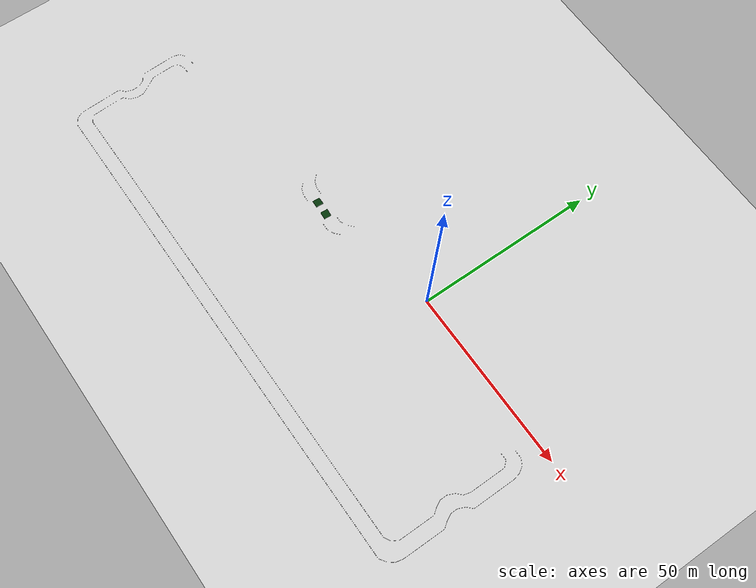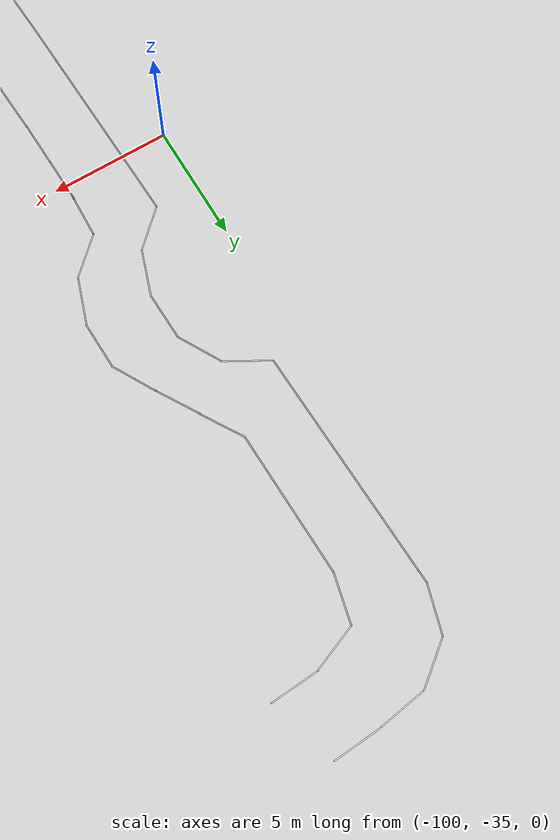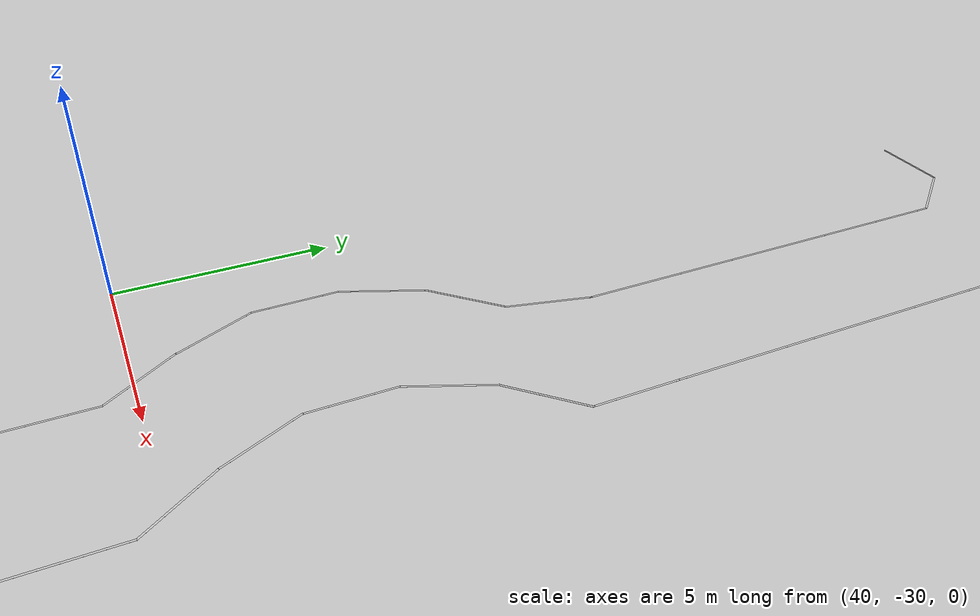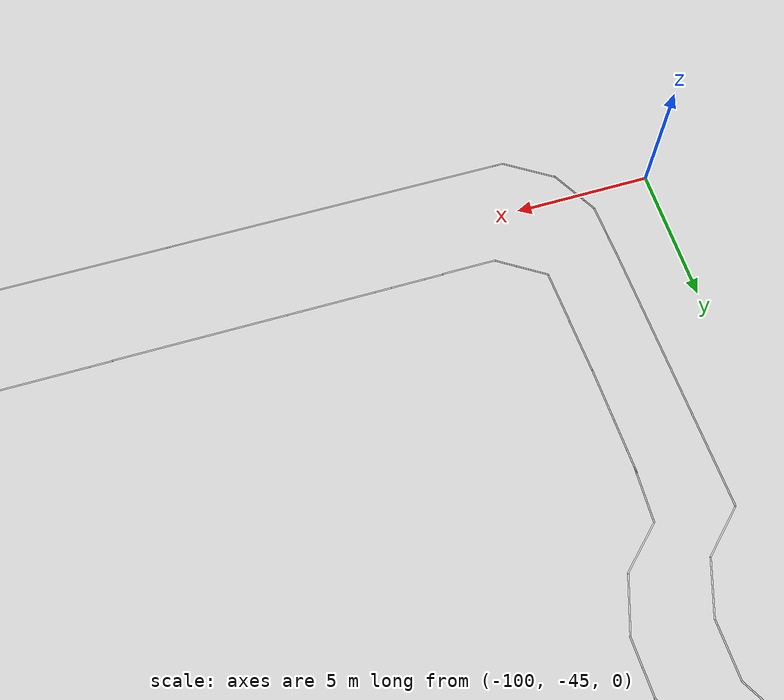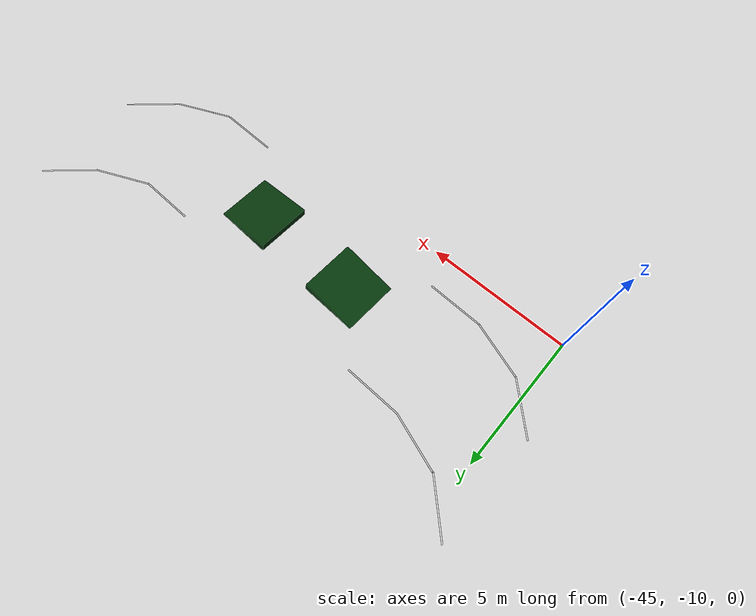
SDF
<sdf version="1.7">
 <world name="default">
  <light name="sun" type="directional">
   <pose>0 0 10 0 -0 0</pose>
   <diffuse>0.8 0.8 0.8 1</diffuse>
   <specular>0.2 0.2 0.2 1</specular>
   <attenuation>
    <range>1000</range>
    <constant>0.9</constant>
    <linear>0.01</linear>
    <quadratic>0.001</quadratic>
   </attenuation>
   <direction>-0.5 0.1 -0.9</direction>
   <spot><inner_angle>0</inner_angle><outer_angle>0</outer_angle><falloff>0</falloff></spot>
  </light>
  <model name="ground_plane">
   <static>1</static>
   <link name="link">
    <collision name="collision">
     <geometry><plane><normal>0 0 1</normal><size>100 100</size></plane></geometry>
     <surface>
      <contact><collide_bitmask>65535</collide_bitmask></contact>
      <friction><ode><mu>100</mu><mu2>50</mu2></ode></friction>
     </surface>
    </collision>
    <visual name="visual">
     <cast_shadows>0</cast_shadows>
     <geometry><plane><normal>0 0 1</normal><size>100 100</size></plane></geometry>
     <material>
      <script><uri>file://media/materials/scripts/gazebo.material</uri><name>Gazebo/Grey</name></script>
     </material>
    </visual>
   </link>
  </model>
  <gravity>0 0 -9.8</gravity>
  <magnetic_field>6e-06 2.3e-05 -4.2e-05</magnetic_field>
  <atmosphere type="adiabatic"/>
  <physics type="ode">
   <max_step_size>0.001</max_step_size>
   <real_time_factor>1</real_time_factor>
   <real_time_update_rate>1000</real_time_update_rate>
  </physics>
  <scene><ambient>0.4 0.4 0.4 1</ambient><background>0.7 0.7 0.7 1</background><shadows>1</shadows></scene>
  <spherical_coordinates>
   <surface_model>EARTH_WGS84</surface_model>
   <latitude_deg>0</latitude_deg>
   <longitude_deg>0</longitude_deg>
   <elevation>0</elevation>
   <heading_deg>0</heading_deg>
  </spherical_coordinates>
  <model name="140m Tape">
   <static>1</static>
   <link name="link">
    <inertial>
     <pose>0 0 0.0175 0 -0 0</pose>
     <mass>10</mass>
     <inertia><ixx>1</ixx><ixy>0</ixy><ixz>0</ixz><iyy>1</iyy><iyz>0</iyz><izz>1</izz></inertia>
    </inertial>
    <collision name="collision">
     <pose>0 0 0.0175 0 -0 0</pose>
     <geometry><mesh><uri>model://140mTape/140mTape.dae</uri></mesh></geometry>
    </collision>
    <visual name="visual"><geometry><mesh><uri>model://140mTape/140mTape.dae</uri></mesh></geometry></visual>
   </link>
   <pose>-21.1513 -47.1539 0 0 -0 0</pose>
  </model>
  <model name="2m Tape">
   <static>1</static>
   <link name="link">
    <inertial>
     <pose>0 0 0.0175 0 -0 0</pose>
     <mass>10</mass>
     <inertia><ixx>1</ixx><ixy>0</ixy><ixz>0</ixz><iyy>1</iyy><iyz>0</iyz><izz>1</izz></inertia>
    </inertial>
    <collision name="collision">
     <pose>0 0 0.0175 0 -0 0</pose>
     <geometry><mesh><uri>model://2mTape/2mTape.dae</uri></mesh></geometry>
    </collision>
    <visual name="visual"><geometry><mesh><uri>model://2mTape/2mTape.dae</uri></mesh></geometry></visual>
   </link>
   <pose>45.6804 -46.5754 0 0 -0 0.601741</pose>
  </model>
  <model name="2m Tape_0">
   <static>1</static>
   <link name="link">
    <inertial>
     <pose>0 0 0.0175 0 -0 0</pose>
     <mass>10</mass>
     <inertia><ixx>1</ixx><ixy>0</ixy><ixz>0</ixz><iyy>1</iyy><iyz>0</iyz><izz>1</izz></inertia>
    </inertial>
    <collision name="collision">
     <pose>0 0 0.0175 0 -0 0</pose>
     <geometry><mesh><uri>model://2mTape/2mTape.dae</uri></mesh></geometry>
    </collision>
    <visual name="visual"><geometry><mesh><uri>model://2mTape/2mTape.dae</uri></mesh></geometry></visual>
   </link>
   <pose>47.1125 -45.2484 0 0 -0 0.895158</pose>
  </model>
  <model name="2m Tape_1">
   <static>1</static>
   <link name="link">
    <inertial>
     <pose>0 0 0.0175 0 -0 0</pose>
     <mass>10</mass>
     <inertia><ixx>1</ixx><ixy>0</ixy><ixz>0</ixz><iyy>1</iyy><iyz>0</iyz><izz>1</izz></inertia>
    </inertial>
    <collision name="collision">
     <pose>0 0 0.0175 0 -0 0</pose>
     <geometry><mesh><uri>model://2mTape/2mTape.dae</uri></mesh></geometry>
    </collision>
    <visual name="visual"><geometry><mesh><uri>model://2mTape/2mTape.dae</uri></mesh></geometry></visual>
   </link>
   <pose>47.9608 -43.482 0 0 -0 1.34892</pose>
  </model>
  <model name="2m Tape_3">
   <static>1</static>
   <link name="link">
    <inertial>
     <pose>0 0 0.0175 0 -0 0</pose>
     <mass>10</mass>
     <inertia><ixx>1</ixx><ixy>0</ixy><ixz>0</ixz><iyy>1</iyy><iyz>0</iyz><izz>1</izz></inertia>
    </inertial>
    <collision name="collision">
     <pose>0 0 0.0175 0 -0 0</pose>
     <geometry><mesh><uri>model://2mTape/2mTape.dae</uri></mesh></geometry>
    </collision>
    <visual name="visual"><geometry><mesh><uri>model://2mTape/2mTape.dae</uri></mesh></geometry></visual>
   </link>
   <pose>48.1967 -41.5182 0 0 -0 1.56187</pose>
  </model>
  <model name="10m Tape_0">
   <static>1</static>
   <link name="link">
    <inertial>
     <pose>0 0 0.0175 0 -0 0</pose>
     <mass>10</mass>
     <inertia><ixx>1</ixx><ixy>0</ixy><ixz>0</ixz><iyy>1</iyy><iyz>0</iyz><izz>1</izz></inertia>
    </inertial>
    <collision name="collision">
     <pose>0 0 0.0175 0 -0 0</pose>
     <geometry><mesh><uri>model://10mTape/10mTape.dae</uri></mesh></geometry>
    </collision>
    <visual name="visual"><geometry><mesh><uri>model://10mTape/10mTape.dae</uri></mesh></geometry></visual>
   </link>
   <pose>48.1366 -35.5288 0 0 0 -1.56635</pose>
  </model>
  <model name="2m Tape_2">
   <static>1</static>
   <link name="link">
    <inertial>
     <pose>0 0 0.0175 0 -0 0</pose>
     <mass>10</mass>
     <inertia><ixx>1</ixx><ixy>0</ixy><ixz>0</ixz><iyy>1</iyy><iyz>0</iyz><izz>1</izz></inertia>
    </inertial>
    <collision name="collision">
     <pose>0 0 0.0175 0 -0 0</pose>
     <geometry><mesh><uri>model://2mTape/2mTape.dae</uri></mesh></geometry>
    </collision>
    <visual name="visual"><geometry><mesh><uri>model://2mTape/2mTape.dae</uri></mesh></geometry></visual>
   </link>
   <pose>47.5374 -29.7551 0 0 0 -0.932759</pose>
  </model>
  <model name="2m Tape_2_clone">
   <static>1</static>
   <link name="link">
    <inertial>
     <pose>0 0 0.0175 0 -0 0</pose>
     <mass>10</mass>
     <inertia><ixx>1</ixx><ixy>0</ixy><ixz>0</ixz><iyy>1</iyy><iyz>0</iyz><izz>1</izz></inertia>
    </inertial>
    <collision name="collision">
     <pose>0 0 0.0175 0 -0 0</pose>
     <geometry><mesh><uri>model://2mTape/2mTape.dae</uri></mesh></geometry>
    </collision>
    <visual name="visual"><geometry><mesh><uri>model://2mTape/2mTape.dae</uri></mesh></geometry></visual>
   </link>
   <pose>46.4948 -28.0704 0 0 0 -1.10193</pose>
  </model>
  <model name="2m Tape_4">
   <static>1</static>
   <link name="link">
    <inertial>
     <pose>0 0 0.0175 0 -0 0</pose>
     <mass>10</mass>
     <inertia><ixx>1</ixx><ixy>0</ixy><ixz>0</ixz><iyy>1</iyy><iyz>0</iyz><izz>1</izz></inertia>
    </inertial>
    <collision name="collision">
     <pose>0 0 0.0175 0 -0 0</pose>
     <geometry><mesh><uri>model://2mTape/2mTape.dae</uri></mesh></geometry>
    </collision>
    <visual name="visual"><geometry><mesh><uri>model://2mTape/2mTape.dae</uri></mesh></geometry></visual>
   </link>
   <pose>46.0419 -26.1884 0 0 0 -1.56173</pose>
  </model>
  <model name="2m Tape_5">
   <static>1</static>
   <link name="link">
    <inertial>
     <pose>0 0 0.0175 0 -0 0</pose>
     <mass>10</mass>
     <inertia><ixx>1</ixx><ixy>0</ixy><ixz>0</ixz><iyy>1</iyy><iyz>0</iyz><izz>1</izz></inertia>
    </inertial>
    <collision name="collision">
     <pose>0 0 0.0175 0 -0 0</pose>
     <geometry><mesh><uri>model://2mTape/2mTape.dae</uri></mesh></geometry>
    </collision>
    <visual name="visual"><geometry><mesh><uri>model://2mTape/2mTape.dae</uri></mesh></geometry></visual>
   </link>
   <pose>46.4353 -24.2739 0 0 0 -1.98171</pose>
  </model>
  <model name="2m Tape_5_clone">
   <static>1</static>
   <link name="link">
    <inertial>
     <pose>0 0 0.0175 0 -0 0</pose>
     <mass>10</mass>
     <inertia><ixx>1</ixx><ixy>0</ixy><ixz>0</ixz><iyy>1</iyy><iyz>0</iyz><izz>1</izz></inertia>
    </inertial>
    <collision name="collision">
     <pose>0 0 0.0175 0 -0 0</pose>
     <geometry><mesh><uri>model://2mTape/2mTape.dae</uri></mesh></geometry>
    </collision>
    <visual name="visual"><geometry><mesh><uri>model://2mTape/2mTape.dae</uri></mesh></geometry></visual>
   </link>
   <pose>47.5583 -22.6619 0 0 0 -2.36892</pose>
  </model>
  <model name="2m Tape_4_clone">
   <static>1</static>
   <link name="link">
    <inertial>
     <pose>0 0 0.0175 0 -0 0</pose>
     <mass>10</mass>
     <inertia><ixx>1</ixx><ixy>0</ixy><ixz>0</ixz><iyy>1</iyy><iyz>0</iyz><izz>1</izz></inertia>
    </inertial>
    <collision name="collision">
     <pose>0 0 0.0175 0 -0 0</pose>
     <geometry><mesh><uri>model://2mTape/2mTape.dae</uri></mesh></geometry>
    </collision>
    <visual name="visual"><geometry><mesh><uri>model://2mTape/2mTape.dae</uri></mesh></geometry></visual>
   </link>
   <pose>48.2399 -21.016 0 0 0 -1.56173</pose>
  </model>
  <model name="10m Tape_1">
   <static>1</static>
   <link name="link">
    <inertial>
     <pose>0 0 0.0175 0 -0 0</pose>
     <mass>10</mass>
     <inertia><ixx>1</ixx><ixy>0</ixy><ixz>0</ixz><iyy>1</iyy><iyz>0</iyz><izz>1</izz></inertia>
    </inertial>
    <collision name="collision">
     <pose>0 0 0.0175 0 -0 0</pose>
     <geometry><mesh><uri>model://10mTape/10mTape.dae</uri></mesh></geometry>
    </collision>
    <visual name="visual"><geometry><mesh><uri>model://10mTape/10mTape.dae</uri></mesh></geometry></visual>
   </link>
   <pose>48.2475 -15.0212 0 0 -0 1.57732</pose>
  </model>
  <model name="2m Tape_6">
   <static>1</static>
   <link name="link">
    <inertial>
     <pose>0 0 0.0175 0 -0 0</pose>
     <mass>10</mass>
     <inertia><ixx>1</ixx><ixy>0</ixy><ixz>0</ixz><iyy>1</iyy><iyz>0</iyz><izz>1</izz></inertia>
    </inertial>
    <collision name="collision">
     <pose>0 0 0.0175 0 -0 0</pose>
     <geometry><mesh><uri>model://2mTape/2mTape.dae</uri></mesh></geometry>
    </collision>
    <visual name="visual"><geometry><mesh><uri>model://2mTape/2mTape.dae</uri></mesh></geometry></visual>
   </link>
   <pose>47.2585 -7.2523 0 0 -0 2.13636</pose>
  </model>
  <model name="2m Tape_7">
   <static>1</static>
   <link name="link">
    <inertial>
     <pose>0 0 0.0175 0 -0 0</pose>
     <mass>10</mass>
     <inertia><ixx>1</ixx><ixy>0</ixy><ixz>0</ixz><iyy>1</iyy><iyz>0</iyz><izz>1</izz></inertia>
    </inertial>
    <collision name="collision">
     <pose>0 0 0.0175 0 -0 0</pose>
     <geometry><mesh><uri>model://2mTape/2mTape.dae</uri></mesh></geometry>
    </collision>
    <visual name="visual"><geometry><mesh><uri>model://2mTape/2mTape.dae</uri></mesh></geometry></visual>
   </link>
   <pose>47.9583 -9.0731 0 0 0 -1.35367</pose>
  </model>
  <model name="2m Tape_8">
   <static>1</static>
   <link name="link">
    <inertial>
     <pose>0 0 0.0175 0 -0 0</pose>
     <mass>10</mass>
     <inertia><ixx>1</ixx><ixy>0</ixy><ixz>0</ixz><iyy>1</iyy><iyz>0</iyz><izz>1</izz></inertia>
    </inertial>
    <collision name="collision">
     <pose>0 0 0.0175 0 -0 0</pose>
     <geometry><mesh><uri>model://2mTape/2mTape.dae</uri></mesh></geometry>
    </collision>
    <visual name="visual"><geometry><mesh><uri>model://2mTape/2mTape.dae</uri></mesh></geometry></visual>
   </link>
   <pose>45.8449 -5.97097 0 0 0 -0.494974</pose>
  </model>
  <model name="2m Tape_9">
   <static>1</static>
   <link name="link">
    <inertial>
     <pose>0 0 0.0175 0 -0 0</pose>
     <mass>10</mass>
     <inertia><ixx>1</ixx><ixy>0</ixy><ixz>0</ixz><iyy>1</iyy><iyz>0</iyz><izz>1</izz></inertia>
    </inertial>
    <collision name="collision">
     <pose>0 0 0.0175 0 -0 0</pose>
     <geometry><mesh><uri>model://2mTape/2mTape.dae</uri></mesh></geometry>
    </collision>
    <visual name="visual"><geometry><mesh><uri>model://2mTape/2mTape.dae</uri></mesh></geometry></visual>
   </link>
   <pose>44.0094 -5.51704 0 0 -0 0</pose>
  </model>
  <model name="2m Tape_3_clone">
   <static>1</static>
   <link name="link">
    <inertial>
     <pose>0 0 0.0175 0 -0 0</pose>
     <mass>10</mass>
     <inertia><ixx>1</ixx><ixy>0</ixy><ixz>0</ixz><iyy>1</iyy><iyz>0</iyz><izz>1</izz></inertia>
    </inertial>
    <collision name="collision">
     <pose>0 0 0.0175 0 -0 0</pose>
     <geometry><mesh><uri>model://2mTape/2mTape.dae</uri></mesh></geometry>
    </collision>
    <visual name="visual"><geometry><mesh><uri>model://2mTape/2mTape.dae</uri></mesh></geometry></visual>
   </link>
   <pose>43.75 -41.4958 0 0 -0 1.06326</pose>
  </model>
  <model name="10m Tape_0_clone">
   <static>1</static>
   <link name="link">
    <inertial>
     <pose>0 0 0.0175 0 -0 0</pose>
     <mass>10</mass>
     <inertia><ixx>1</ixx><ixy>0</ixy><ixz>0</ixz><iyy>1</iyy><iyz>0</iyz><izz>1</izz></inertia>
    </inertial>
    <collision name="collision">
     <pose>0 0 0.0175 0 -0 0</pose>
     <geometry><mesh><uri>model://10mTape/10mTape.dae</uri></mesh></geometry>
    </collision>
    <visual name="visual"><geometry><mesh><uri>model://10mTape/10mTape.dae</uri></mesh></geometry></visual>
   </link>
   <pose>44.1682 -35.6366 0 0 0 -1.56635</pose>
  </model>
  <model name="2m Tape_2_clone_0">
   <static>1</static>
   <link name="link">
    <inertial>
     <pose>0 0 0.0175 0 -0 0</pose>
     <mass>10</mass>
     <inertia><ixx>1</ixx><ixy>0</ixy><ixz>0</ixz><iyy>1</iyy><iyz>0</iyz><izz>1</izz></inertia>
    </inertial>
    <collision name="collision">
     <pose>0 0 0.0175 0 -0 0</pose>
     <geometry><mesh><uri>model://2mTape/2mTape.dae</uri></mesh></geometry>
    </collision>
    <visual name="visual"><geometry><mesh><uri>model://2mTape/2mTape.dae</uri></mesh></geometry></visual>
   </link>
   <pose>43.5511 -29.853 0 0 0 -0.932759</pose>
  </model>
  <model name="2m Tape_2_clone_clone">
   <static>1</static>
   <link name="link">
    <inertial>
     <pose>0 0 0.0175 0 -0 0</pose>
     <mass>10</mass>
     <inertia><ixx>1</ixx><ixy>0</ixy><ixz>0</ixz><iyy>1</iyy><iyz>0</iyz><izz>1</izz></inertia>
    </inertial>
    <collision name="collision">
     <pose>0 0 0.0175 0 -0 0</pose>
     <geometry><mesh><uri>model://2mTape/2mTape.dae</uri></mesh></geometry>
    </collision>
    <visual name="visual"><geometry><mesh><uri>model://2mTape/2mTape.dae</uri></mesh></geometry></visual>
   </link>
   <pose>42.5314 -28.1777 0 0 0 -1.10193</pose>
  </model>
  <model name="2m Tape_4_clone_0">
   <static>1</static>
   <link name="link">
    <inertial>
     <pose>0 0 0.0175 0 -0 0</pose>
     <mass>10</mass>
     <inertia><ixx>1</ixx><ixy>0</ixy><ixz>0</ixz><iyy>1</iyy><iyz>0</iyz><izz>1</izz></inertia>
    </inertial>
    <collision name="collision">
     <pose>0 0 0.0175 0 -0 0</pose>
     <geometry><mesh><uri>model://2mTape/2mTape.dae</uri></mesh></geometry>
    </collision>
    <visual name="visual"><geometry><mesh><uri>model://2mTape/2mTape.dae</uri></mesh></geometry></visual>
   </link>
   <pose>42.0708 -26.2912 0 0 0 -1.56173</pose>
  </model>
  <model name="2m Tape_5_clone_0">
   <static>1</static>
   <link name="link">
    <inertial>
     <pose>0 0 0.0175 0 -0 0</pose>
     <mass>10</mass>
     <inertia><ixx>1</ixx><ixy>0</ixy><ixz>0</ixz><iyy>1</iyy><iyz>0</iyz><izz>1</izz></inertia>
    </inertial>
    <collision name="collision">
     <pose>0 0 0.0175 0 -0 0</pose>
     <geometry><mesh><uri>model://2mTape/2mTape.dae</uri></mesh></geometry>
    </collision>
    <visual name="visual"><geometry><mesh><uri>model://2mTape/2mTape.dae</uri></mesh></geometry></visual>
   </link>
   <pose>42.4557 -24.3839 0 0 0 -1.98171</pose>
  </model>
  <model name="2m Tape_5_clone_clone">
   <static>1</static>
   <link name="link">
    <inertial>
     <pose>0 0 0.0175 0 -0 0</pose>
     <mass>10</mass>
     <inertia><ixx>1</ixx><ixy>0</ixy><ixz>0</ixz><iyy>1</iyy><iyz>0</iyz><izz>1</izz></inertia>
    </inertial>
    <collision name="collision">
     <pose>0 0 0.0175 0 -0 0</pose>
     <geometry><mesh><uri>model://2mTape/2mTape.dae</uri></mesh></geometry>
    </collision>
    <visual name="visual"><geometry><mesh><uri>model://2mTape/2mTape.dae</uri></mesh></geometry></visual>
   </link>
   <pose>43.5617 -22.768 0 0 0 -2.36892</pose>
  </model>
  <model name="2m Tape_4_clone_clone">
   <static>1</static>
   <link name="link">
    <inertial>
     <pose>0 0 0.0175 0 -0 0</pose>
     <mass>10</mass>
     <inertia><ixx>1</ixx><ixy>0</ixy><ixz>0</ixz><iyy>1</iyy><iyz>0</iyz><izz>1</izz></inertia>
    </inertial>
    <collision name="collision">
     <pose>0 0 0.0175 0 -0 0</pose>
     <geometry><mesh><uri>model://2mTape/2mTape.dae</uri></mesh></geometry>
    </collision>
    <visual name="visual"><geometry><mesh><uri>model://2mTape/2mTape.dae</uri></mesh></geometry></visual>
   </link>
   <pose>44.5117 -21.1143 0 0 0 -1.80701</pose>
  </model>
  <model name="10m Tape_1_clone">
   <static>1</static>
   <link name="link">
    <inertial>
     <pose>0 0 0.0175 0 -0 0</pose>
     <mass>10</mass>
     <inertia><ixx>1</ixx><ixy>0</ixy><ixz>0</ixz><iyy>1</iyy><iyz>0</iyz><izz>1</izz></inertia>
    </inertial>
    <collision name="collision">
     <pose>0 0 0.0175 0 -0 0</pose>
     <geometry><mesh><uri>model://10mTape/10mTape.dae</uri></mesh></geometry>
    </collision>
    <visual name="visual"><geometry><mesh><uri>model://10mTape/10mTape.dae</uri></mesh></geometry></visual>
   </link>
   <pose>44.7584 -15.2024 0 0 -0 1.57732</pose>
  </model>
  <model name="2m Tape_7_clone">
   <static>1</static>
   <link name="link">
    <inertial>
     <pose>0 0 0.0175 0 -0 0</pose>
     <mass>10</mass>
     <inertia><ixx>1</ixx><ixy>0</ixy><ixz>0</ixz><iyy>1</iyy><iyz>0</iyz><izz>1</izz></inertia>
    </inertial>
    <collision name="collision">
     <pose>0 0 0.0175 0 -0 0</pose>
     <geometry><mesh><uri>model://2mTape/2mTape.dae</uri></mesh></geometry>
    </collision>
    <visual name="visual"><geometry><mesh><uri>model://2mTape/2mTape.dae</uri></mesh></geometry></visual>
   </link>
   <pose>44.0321 -9.47602 0 0 0 -0.856035</pose>
  </model>
  <model name="2m Tape_7_clone_clone_clone">
   <static>1</static>
   <link name="link">
    <inertial>
     <pose>0 0 0.0175 0 -0 0</pose>
     <mass>10</mass>
     <inertia><ixx>1</ixx><ixy>0</ixy><ixz>0</ixz><iyy>1</iyy><iyz>0</iyz><izz>1</izz></inertia>
    </inertial>
    <collision name="collision">
     <pose>0 0 0.0175 0 -0 0</pose>
     <geometry><mesh><uri>model://2mTape/2mTape.dae</uri></mesh></geometry>
    </collision>
    <visual name="visual"><geometry><mesh><uri>model://2mTape/2mTape.dae</uri></mesh></geometry></visual>
   </link>
   <pose>42.4047 -8.73878 0 0 -0 0.006809</pose>
  </model>
  <model name="2m Tape_3_clone_clone">
   <static>1</static>
   <link name="link">
    <inertial>
     <pose>0 0 0.0175 0 -0 0</pose>
     <mass>10</mass>
     <inertia><ixx>1</ixx><ixy>0</ixy><ixz>0</ixz><iyy>1</iyy><iyz>0</iyz><izz>1</izz></inertia>
    </inertial>
    <collision name="collision">
     <pose>0 0 0.0175 0 -0 0</pose>
     <geometry><mesh><uri>model://2mTape/2mTape.dae</uri></mesh></geometry>
    </collision>
    <visual name="visual"><geometry><mesh><uri>model://2mTape/2mTape.dae</uri></mesh></geometry></visual>
   </link>
   <pose>42.4131 -42.8564 0 0 -0 0.506337</pose>
  </model>
  <model name="2m Tape_10">
   <static>1</static>
   <link name="link">
    <inertial>
     <pose>0 0 0.0175 0 -0 0</pose>
     <mass>10</mass>
     <inertia><ixx>1</ixx><ixy>0</ixy><ixz>0</ixz><iyy>1</iyy><iyz>0</iyz><izz>1</izz></inertia>
    </inertial>
    <collision name="collision">
     <pose>0 0 0.0175 0 -0 0</pose>
     <geometry><mesh><uri>model://2mTape/2mTape.dae</uri></mesh></geometry>
    </collision>
    <visual name="visual"><geometry><mesh><uri>model://2mTape/2mTape.dae</uri></mesh></geometry></visual>
   </link>
   <pose>40.5363 -43.3329 0 0 -0 0</pose>
  </model>
  <model name="2m Tape_11">
   <static>1</static>
   <link name="link">
    <inertial>
     <pose>0 0 0.0175 0 -0 0</pose>
     <mass>10</mass>
     <inertia><ixx>1</ixx><ixy>0</ixy><ixz>0</ixz><iyy>1</iyy><iyz>0</iyz><izz>1</izz></inertia>
    </inertial>
    <collision name="collision">
     <pose>0 0 0.0175 0 -0 0</pose>
     <geometry><mesh><uri>model://2mTape/2mTape.dae</uri></mesh></geometry>
    </collision>
    <visual name="visual"><geometry><mesh><uri>model://2mTape/2mTape.dae</uri></mesh></geometry></visual>
   </link>
   <pose>-95.9813 -46.5979 0 0 0 -0.580554</pose>
  </model>
  <model name="2m Tape_12">
   <static>1</static>
   <link name="link">
    <inertial>
     <pose>0 0 0.0175 0 -0 0</pose>
     <mass>10</mass>
     <inertia><ixx>1</ixx><ixy>0</ixy><ixz>0</ixz><iyy>1</iyy><iyz>0</iyz><izz>1</izz></inertia>
    </inertial>
    <collision name="collision">
     <pose>0 0 0.0175 0 -0 0</pose>
     <geometry><mesh><uri>model://2mTape/2mTape.dae</uri></mesh></geometry>
    </collision>
    <visual name="visual"><geometry><mesh><uri>model://2mTape/2mTape.dae</uri></mesh></geometry></visual>
   </link>
   <pose>-97.2863 -45.1975 0 0 0 -1.07615</pose>
  </model>
  <model name="2m Tape_12_clone">
   <static>1</static>
   <link name="link">
    <inertial>
     <pose>0 0 0.0175 0 -0 0</pose>
     <mass>10</mass>
     <inertia><ixx>1</ixx><ixy>0</ixy><ixz>0</ixz><iyy>1</iyy><iyz>0</iyz><izz>1</izz></inertia>
    </inertial>
    <collision name="collision">
     <pose>0 0 0.0175 0 -0 0</pose>
     <geometry><mesh><uri>model://2mTape/2mTape.dae</uri></mesh></geometry>
    </collision>
    <visual name="visual"><geometry><mesh><uri>model://2mTape/2mTape.dae</uri></mesh></geometry></visual>
   </link>
   <pose>-97.796 -43.3342 0 0 0 -1.52067</pose>
  </model>
  <model name="10m Tape">
   <static>1</static>
   <link name="link">
    <inertial>
     <pose>0 0 0.0175 0 -0 0</pose>
     <mass>10</mass>
     <inertia><ixx>1</ixx><ixy>0</ixy><ixz>0</ixz><iyy>1</iyy><iyz>0</iyz><izz>1</izz></inertia>
    </inertial>
    <collision name="collision">
     <pose>0 0 0.0175 0 -0 0</pose>
     <geometry><mesh><uri>model://10mTape/10mTape.dae</uri></mesh></geometry>
    </collision>
    <visual name="visual"><geometry><mesh><uri>model://10mTape/10mTape.dae</uri></mesh></geometry></visual>
   </link>
   <pose>-98.0198 -37.3488 0 0 0 -1.53628</pose>
  </model>
  <model name="2m Tape_13">
   <static>1</static>
   <link name="link">
    <inertial>
     <pose>0 0 0.0175 0 -0 0</pose>
     <mass>10</mass>
     <inertia><ixx>1</ixx><ixy>0</ixy><ixz>0</ixz><iyy>1</iyy><iyz>0</iyz><izz>1</izz></inertia>
    </inertial>
    <collision name="collision">
     <pose>0 0 0.0175 0 -0 0</pose>
     <geometry><mesh><uri>model://2mTape/2mTape.dae</uri></mesh></geometry>
    </collision>
    <visual name="visual"><geometry><mesh><uri>model://2mTape/2mTape.dae</uri></mesh></geometry></visual>
   </link>
   <pose>-97.423 -31.7074 0 0 -0 0.750379</pose>
  </model>
  <model name="2m Tape_13_clone">
   <static>1</static>
   <link name="link">
    <inertial>
     <pose>0 0 0.0175 0 -0 0</pose>
     <mass>10</mass>
     <inertia><ixx>1</ixx><ixy>0</ixy><ixz>0</ixz><iyy>1</iyy><iyz>0</iyz><izz>1</izz></inertia>
    </inertial>
    <collision name="collision">
     <pose>0 0 0.0175 0 -0 0</pose>
     <geometry><mesh><uri>model://2mTape/2mTape.dae</uri></mesh></geometry>
    </collision>
    <visual name="visual"><geometry><mesh><uri>model://2mTape/2mTape.dae</uri></mesh></geometry></visual>
   </link>
   <pose>-96.3785 -30.0927 0 0 -0 1.23809</pose>
  </model>
  <model name="2m Tape_13_clone_clone">
   <static>1</static>
   <link name="link">
    <inertial>
     <pose>0 0 0.0175 0 -0 0</pose>
     <mass>10</mass>
     <inertia><ixx>1</ixx><ixy>0</ixy><ixz>0</ixz><iyy>1</iyy><iyz>0</iyz><izz>1</izz></inertia>
    </inertial>
    <collision name="collision">
     <pose>0 0 0.0175 0 -0 0</pose>
     <geometry><mesh><uri>model://2mTape/2mTape.dae</uri></mesh></geometry>
    </collision>
    <visual name="visual"><geometry><mesh><uri>model://2mTape/2mTape.dae</uri></mesh></geometry></visual>
   </link>
   <pose>-96.0833 -28.1588 0 0 -0 1.59632</pose>
  </model>
  <model name="2m Tape_13_clone_clone_clone">
   <static>1</static>
   <link name="link">
    <inertial>
     <pose>0 0 0.0175 0 -0 0</pose>
     <mass>10</mass>
     <inertia><ixx>1</ixx><ixy>0</ixy><ixz>0</ixz><iyy>1</iyy><iyz>0</iyz><izz>1</izz></inertia>
    </inertial>
    <collision name="collision">
     <pose>0 0 0.0175 0 -0 0</pose>
     <geometry><mesh><uri>model://2mTape/2mTape.dae</uri></mesh></geometry>
    </collision>
    <visual name="visual"><geometry><mesh><uri>model://2mTape/2mTape.dae</uri></mesh></geometry></visual>
   </link>
   <pose>-96.5819 -26.2899 0 0 -0 2.07673</pose>
  </model>
  <model name="2m Tape_13_clone_clone_clone_clone">
   <static>1</static>
   <link name="link">
    <inertial>
     <pose>0 0 0.0175 0 -0 0</pose>
     <mass>10</mass>
     <inertia><ixx>1</ixx><ixy>0</ixy><ixz>0</ixz><iyy>1</iyy><iyz>0</iyz><izz>1</izz></inertia>
    </inertial>
    <collision name="collision">
     <pose>0 0 0.0175 0 -0 0</pose>
     <geometry><mesh><uri>model://2mTape/2mTape.dae</uri></mesh></geometry>
    </collision>
    <visual name="visual"><geometry><mesh><uri>model://2mTape/2mTape.dae</uri></mesh></geometry></visual>
   </link>
   <pose>-97.9223 -24.9224 0 0 -0 2.62036</pose>
  </model>
  <model name="10m Tape_clone">
   <static>1</static>
   <link name="link">
    <inertial>
     <pose>0 0 0.0175 0 -0 0</pose>
     <mass>10</mass>
     <inertia><ixx>1</ixx><ixy>0</ixy><ixz>0</ixz><iyy>1</iyy><iyz>0</iyz><izz>1</izz></inertia>
    </inertial>
    <collision name="collision">
     <pose>0 0 0.0175 0 -0 0</pose>
     <geometry><mesh><uri>model://10mTape/10mTape.dae</uri></mesh></geometry>
    </collision>
    <visual name="visual"><geometry><mesh><uri>model://10mTape/10mTape.dae</uri></mesh></geometry></visual>
   </link>
   <pose>-98.9827 -19.4688 0 0 0 -1.53628</pose>
  </model>
  <model name="2m Tape_14">
   <static>1</static>
   <link name="link">
    <inertial>
     <pose>0 0 0.0175 0 -0 0</pose>
     <mass>10</mass>
     <inertia><ixx>1</ixx><ixy>0</ixy><ixz>0</ixz><iyy>1</iyy><iyz>0</iyz><izz>1</izz></inertia>
    </inertial>
    <collision name="collision">
     <pose>0 0 0.0175 0 -0 0</pose>
     <geometry><mesh><uri>model://2mTape/2mTape.dae</uri></mesh></geometry>
    </collision>
    <visual name="visual"><geometry><mesh><uri>model://2mTape/2mTape.dae</uri></mesh></geometry></visual>
   </link>
   <pose>-98.8729 -13.5437 0 0 0 -1.86679</pose>
  </model>
  <model name="2m Tape_14_clone">
   <static>1</static>
   <link name="link">
    <inertial>
     <pose>0 0 0.0175 0 -0 0</pose>
     <mass>10</mass>
     <inertia><ixx>1</ixx><ixy>0</ixy><ixz>0</ixz><iyy>1</iyy><iyz>0</iyz><izz>1</izz></inertia>
    </inertial>
    <collision name="collision">
     <pose>0 0 0.0175 0 -0 0</pose>
     <geometry><mesh><uri>model://2mTape/2mTape.dae</uri></mesh></geometry>
    </collision>
    <visual name="visual"><geometry><mesh><uri>model://2mTape/2mTape.dae</uri></mesh></geometry></visual>
   </link>
   <pose>-97.773 -11.9974 0 0 0 -2.50053</pose>
  </model>
  <model name="2m Tape_14_clone_clone">
   <static>1</static>
   <link name="link">
    <inertial>
     <pose>0 0 0.0175 0 -0 0</pose>
     <mass>10</mass>
     <inertia><ixx>1</ixx><ixy>0</ixy><ixz>0</ixz><iyy>1</iyy><iyz>0</iyz><izz>1</izz></inertia>
    </inertial>
    <collision name="collision">
     <pose>0 0 0.0175 0 -0 0</pose>
     <geometry><mesh><uri>model://2mTape/2mTape.dae</uri></mesh></geometry>
    </collision>
    <visual name="visual"><geometry><mesh><uri>model://2mTape/2mTape.dae</uri></mesh></geometry></visual>
   </link>
   <pose>-95.9904 -11.2785 0 0 0 -3.01216</pose>
  </model>
  <model name="2m Tape_14_clone_clone_clone">
   <static>1</static>
   <link name="link">
    <inertial>
     <pose>0 0 0.0175 0 -0 0</pose>
     <mass>10</mass>
     <inertia><ixx>1</ixx><ixy>0</ixy><ixz>0</ixz><iyy>1</iyy><iyz>0</iyz><izz>1</izz></inertia>
    </inertial>
    <collision name="collision">
     <pose>0 0 0.0175 0 -0 0</pose>
     <geometry><mesh><uri>model://2mTape/2mTape.dae</uri></mesh></geometry>
    </collision>
    <visual name="visual"><geometry><mesh><uri>model://2mTape/2mTape.dae</uri></mesh></geometry></visual>
   </link>
   <pose>-94.0323 -11.1005 0 0 0 -3.09641</pose>
  </model>
  <model name="10m Tape_2">
   <static>1</static>
   <link name="link">
    <inertial>
     <pose>0 0 0.0175 0 -0 0</pose>
     <mass>10</mass>
     <inertia><ixx>1</ixx><ixy>0</ixy><ixz>0</ixz><iyy>1</iyy><iyz>0</iyz><izz>1</izz></inertia>
    </inertial>
    <collision name="collision">
     <pose>0 0 0.0175 0 -0 0</pose>
     <geometry><mesh><uri>model://10mTape/10mTape.dae</uri></mesh></geometry>
    </collision>
    <visual name="visual"><geometry><mesh><uri>model://10mTape/10mTape.dae</uri></mesh></geometry></visual>
   </link>
   <pose>34.6028 -43.3327 0 0 -0 0</pose>
  </model>
  <model name="10m Tape_2_clone">
   <static>1</static>
   <link name="link">
    <inertial>
     <pose>0 0 0.0175 0 -0 0</pose>
     <mass>10</mass>
     <inertia><ixx>1</ixx><ixy>0</ixy><ixz>0</ixz><iyy>1</iyy><iyz>0</iyz><izz>1</izz></inertia>
    </inertial>
    <collision name="collision">
     <pose>0 0 0.0175 0 -0 0</pose>
     <geometry><mesh><uri>model://10mTape/10mTape.dae</uri></mesh></geometry>
    </collision>
    <visual name="visual"><geometry><mesh><uri>model://10mTape/10mTape.dae</uri></mesh></geometry></visual>
   </link>
   <pose>24.6515 -43.3446 0 0 -0 0</pose>
  </model>
  <model name="10m Tape_2_clone_0">
   <static>1</static>
   <link name="link">
    <inertial>
     <pose>0 0 0.0175 0 -0 0</pose>
     <mass>10</mass>
     <inertia><ixx>1</ixx><ixy>0</ixy><ixz>0</ixz><iyy>1</iyy><iyz>0</iyz><izz>1</izz></inertia>
    </inertial>
    <collision name="collision">
     <pose>0 0 0.0175 0 -0 0</pose>
     <geometry><mesh><uri>model://10mTape/10mTape.dae</uri></mesh></geometry>
    </collision>
    <visual name="visual"><geometry><mesh><uri>model://10mTape/10mTape.dae</uri></mesh></geometry></visual>
   </link>
   <pose>14.6807 -43.3342 0 0 -0 0</pose>
  </model>
  <model name="10m Tape_2_clone_1">
   <static>1</static>
   <link name="link">
    <inertial>
     <pose>0 0 0.0175 0 -0 0</pose>
     <mass>10</mass>
     <inertia><ixx>1</ixx><ixy>0</ixy><ixz>0</ixz><iyy>1</iyy><iyz>0</iyz><izz>1</izz></inertia>
    </inertial>
    <collision name="collision">
     <pose>0 0 0.0175 0 -0 0</pose>
     <geometry><mesh><uri>model://10mTape/10mTape.dae</uri></mesh></geometry>
    </collision>
    <visual name="visual"><geometry><mesh><uri>model://10mTape/10mTape.dae</uri></mesh></geometry></visual>
   </link>
   <pose>4.71754 -43.3305 0 0 -0 0</pose>
  </model>
  <model name="10m Tape_2_clone_2">
   <static>1</static>
   <link name="link">
    <inertial>
     <pose>0 0 0.0175 0 -0 0</pose>
     <mass>10</mass>
     <inertia><ixx>1</ixx><ixy>0</ixy><ixz>0</ixz><iyy>1</iyy><iyz>0</iyz><izz>1</izz></inertia>
    </inertial>
    <collision name="collision">
     <pose>0 0 0.0175 0 -0 0</pose>
     <geometry><mesh><uri>model://10mTape/10mTape.dae</uri></mesh></geometry>
    </collision>
    <visual name="visual"><geometry><mesh><uri>model://10mTape/10mTape.dae</uri></mesh></geometry></visual>
   </link>
   <pose>-5.22647 -43.3267 0 0 -0 0</pose>
  </model>
  <model name="10m Tape_2_clone_3">
   <static>1</static>
   <link name="link">
    <inertial>
     <pose>0 0 0.0175 0 -0 0</pose>
     <mass>10</mass>
     <inertia><ixx>1</ixx><ixy>0</ixy><ixz>0</ixz><iyy>1</iyy><iyz>0</iyz><izz>1</izz></inertia>
    </inertial>
    <collision name="collision">
     <pose>0 0 0.0175 0 -0 0</pose>
     <geometry><mesh><uri>model://10mTape/10mTape.dae</uri></mesh></geometry>
    </collision>
    <visual name="visual"><geometry><mesh><uri>model://10mTape/10mTape.dae</uri></mesh></geometry></visual>
   </link>
   <pose>-15.1669 -43.3235 0 0 -0 0</pose>
  </model>
  <model name="10m Tape_2_clone_4">
   <static>1</static>
   <link name="link">
    <inertial>
     <pose>0 0 0.0175 0 -0 0</pose>
     <mass>10</mass>
     <inertia><ixx>1</ixx><ixy>0</ixy><ixz>0</ixz><iyy>1</iyy><iyz>0</iyz><izz>1</izz></inertia>
    </inertial>
    <collision name="collision">
     <pose>0 0 0.0175 0 -0 0</pose>
     <geometry><mesh><uri>model://10mTape/10mTape.dae</uri></mesh></geometry>
    </collision>
    <visual name="visual"><geometry><mesh><uri>model://10mTape/10mTape.dae</uri></mesh></geometry></visual>
   </link>
   <pose>-25.1517 -43.3231 0 0 -0 0</pose>
  </model>
  <model name="10m Tape_2_clone_5">
   <static>1</static>
   <link name="link">
    <inertial>
     <pose>0 0 0.0175 0 -0 0</pose>
     <mass>10</mass>
     <inertia><ixx>1</ixx><ixy>0</ixy><ixz>0</ixz><iyy>1</iyy><iyz>0</iyz><izz>1</izz></inertia>
    </inertial>
    <collision name="collision">
     <pose>0 0 0.0175 0 -0 0</pose>
     <geometry><mesh><uri>model://10mTape/10mTape.dae</uri></mesh></geometry>
    </collision>
    <visual name="visual"><geometry><mesh><uri>model://10mTape/10mTape.dae</uri></mesh></geometry></visual>
   </link>
   <pose>-35.0691 -43.3172 0 0 -0 0</pose>
  </model>
  <model name="10m Tape_2_clone_6">
   <static>1</static>
   <link name="link">
    <inertial>
     <pose>0 0 0.0175 0 -0 0</pose>
     <mass>10</mass>
     <inertia><ixx>1</ixx><ixy>0</ixy><ixz>0</ixz><iyy>1</iyy><iyz>0</iyz><izz>1</izz></inertia>
    </inertial>
    <collision name="collision">
     <pose>0 0 0.0175 0 -0 0</pose>
     <geometry><mesh><uri>model://10mTape/10mTape.dae</uri></mesh></geometry>
    </collision>
    <visual name="visual"><geometry><mesh><uri>model://10mTape/10mTape.dae</uri></mesh></geometry></visual>
   </link>
   <pose>-44.9958 -43.3015 0 0 -0 0</pose>
  </model>
  <model name="10m Tape_2_clone_7">
   <static>1</static>
   <link name="link">
    <inertial>
     <pose>0 0 0.0175 0 -0 0</pose>
     <mass>10</mass>
     <inertia><ixx>1</ixx><ixy>0</ixy><ixz>0</ixz><iyy>1</iyy><iyz>0</iyz><izz>1</izz></inertia>
    </inertial>
    <collision name="collision">
     <pose>0 0 0.0175 0 -0 0</pose>
     <geometry><mesh><uri>model://10mTape/10mTape.dae</uri></mesh></geometry>
    </collision>
    <visual name="visual"><geometry><mesh><uri>model://10mTape/10mTape.dae</uri></mesh></geometry></visual>
   </link>
   <pose>-54.888 -43.3077 0 0 -0 0</pose>
  </model>
  <model name="10m Tape_2_clone_8">
   <static>1</static>
   <link name="link">
    <inertial>
     <pose>0 0 0.0175 0 -0 0</pose>
     <mass>10</mass>
     <inertia><ixx>1</ixx><ixy>0</ixy><ixz>0</ixz><iyy>1</iyy><iyz>0</iyz><izz>1</izz></inertia>
    </inertial>
    <collision name="collision">
     <pose>0 0 0.0175 0 -0 0</pose>
     <geometry><mesh><uri>model://10mTape/10mTape.dae</uri></mesh></geometry>
    </collision>
    <visual name="visual"><geometry><mesh><uri>model://10mTape/10mTape.dae</uri></mesh></geometry></visual>
   </link>
   <pose>-64.7986 -43.2913 0 0 -0 0</pose>
  </model>
  <model name="10m Tape_2_clone_9">
   <static>1</static>
   <link name="link">
    <inertial>
     <pose>0 0 0.0175 0 -0 0</pose>
     <mass>10</mass>
     <inertia><ixx>1</ixx><ixy>0</ixy><ixz>0</ixz><iyy>1</iyy><iyz>0</iyz><izz>1</izz></inertia>
    </inertial>
    <collision name="collision">
     <pose>0 0 0.0175 0 -0 0</pose>
     <geometry><mesh><uri>model://10mTape/10mTape.dae</uri></mesh></geometry>
    </collision>
    <visual name="visual"><geometry><mesh><uri>model://10mTape/10mTape.dae</uri></mesh></geometry></visual>
   </link>
   <pose>-74.7648 -43.2761 0 0 -0 0</pose>
  </model>
  <model name="10m Tape_2_clone_10">
   <static>1</static>
   <link name="link">
    <inertial>
     <pose>0 0 0.0175 0 -0 0</pose>
     <mass>10</mass>
     <inertia><ixx>1</ixx><ixy>0</ixy><ixz>0</ixz><iyy>1</iyy><iyz>0</iyz><izz>1</izz></inertia>
    </inertial>
    <collision name="collision">
     <pose>0 0 0.0175 0 -0 0</pose>
     <geometry><mesh><uri>model://10mTape/10mTape.dae</uri></mesh></geometry>
    </collision>
    <visual name="visual"><geometry><mesh><uri>model://10mTape/10mTape.dae</uri></mesh></geometry></visual>
   </link>
   <pose>-84.6785 -43.2903 0 0 -0 0</pose>
  </model>
  <model name="2m Tape_15">
   <static>1</static>
   <link name="link">
    <inertial>
     <pose>0 0 0.0175 0 -0 0</pose>
     <mass>10</mass>
     <inertia><ixx>1</ixx><ixy>0</ixy><ixz>0</ixz><iyy>1</iyy><iyz>0</iyz><izz>1</izz></inertia>
    </inertial>
    <collision name="collision">
     <pose>0 0 0.0175 0 -0 0</pose>
     <geometry><mesh><uri>model://2mTape/2mTape.dae</uri></mesh></geometry>
    </collision>
    <visual name="visual"><geometry><mesh><uri>model://2mTape/2mTape.dae</uri></mesh></geometry></visual>
   </link>
   <pose>-90.6515 -43.2939 0 0 -0 0</pose>
  </model>
  <model name="2m Tape_15_clone_0">
   <static>1</static>
   <link name="link">
    <inertial>
     <pose>0 0 0.0175 0 -0 0</pose>
     <mass>10</mass>
     <inertia><ixx>1</ixx><ixy>0</ixy><ixz>0</ixz><iyy>1</iyy><iyz>0</iyz><izz>1</izz></inertia>
    </inertial>
    <collision name="collision">
     <pose>0 0 0.0175 0 -0 0</pose>
     <geometry><mesh><uri>model://2mTape/2mTape.dae</uri></mesh></geometry>
    </collision>
    <visual name="visual"><geometry><mesh><uri>model://2mTape/2mTape.dae</uri></mesh></geometry></visual>
   </link>
   <pose>-94.3867 -42.7636 0 0 0 -0.580462</pose>
  </model>
  <model name="2m Tape_15_clone">
   <static>1</static>
   <link name="link">
    <inertial>
     <pose>0 0 0.0175 0 -0 0</pose>
     <mass>10</mass>
     <inertia><ixx>1</ixx><ixy>0</ixy><ixz>0</ixz><iyy>1</iyy><iyz>0</iyz><izz>1</izz></inertia>
    </inertial>
    <collision name="collision">
     <pose>0 0 0.0175 0 -0 0</pose>
     <geometry><mesh><uri>model://2mTape/2mTape.dae</uri></mesh></geometry>
    </collision>
    <visual name="visual"><geometry><mesh><uri>model://2mTape/2mTape.dae</uri></mesh></geometry></visual>
   </link>
   <pose>-92.5891 -43.3119 0 0 -0 0</pose>
  </model>
  <model name="2m Tape_15_clone_0_clone">
   <static>1</static>
   <link name="link">
    <inertial>
     <pose>0 0 0.0175 0 -0 0</pose>
     <mass>10</mass>
     <inertia><ixx>1</ixx><ixy>0</ixy><ixz>0</ixz><iyy>1</iyy><iyz>0</iyz><izz>1</izz></inertia>
    </inertial>
    <collision name="collision">
     <pose>0 0 0.0175 0 -0 0</pose>
     <geometry><mesh><uri>model://2mTape/2mTape.dae</uri></mesh></geometry>
    </collision>
    <visual name="visual"><geometry><mesh><uri>model://2mTape/2mTape.dae</uri></mesh></geometry></visual>
   </link>
   <pose>-95.2588 -41.223 0 0 0 -1.51813</pose>
  </model>
  <model name="2m Tape_15_clone_0_clone_clone">
   <static>1</static>
   <link name="link">
    <inertial>
     <pose>0 0 0.0175 0 -0 0</pose>
     <mass>10</mass>
     <inertia><ixx>1</ixx><ixy>0</ixy><ixz>0</ixz><iyy>1</iyy><iyz>0</iyz><izz>1</izz></inertia>
    </inertial>
    <collision name="collision">
     <pose>0 0 0.0175 0 -0 0</pose>
     <geometry><mesh><uri>model://2mTape/2mTape.dae</uri></mesh></geometry>
    </collision>
    <visual name="visual"><geometry><mesh><uri>model://2mTape/2mTape.dae</uri></mesh></geometry></visual>
   </link>
   <pose>-95.3571 -39.2275 0 0 0 -1.51813</pose>
  </model>
  <model name="2m Tape_15_clone_0_clone_clone_0">
   <static>1</static>
   <link name="link">
    <inertial>
     <pose>0 0 0.0175 0 -0 0</pose>
     <mass>10</mass>
     <inertia><ixx>1</ixx><ixy>0</ixy><ixz>0</ixz><iyy>1</iyy><iyz>0</iyz><izz>1</izz></inertia>
    </inertial>
    <collision name="collision">
     <pose>0 0 0.0175 0 -0 0</pose>
     <geometry><mesh><uri>model://2mTape/2mTape.dae</uri></mesh></geometry>
    </collision>
    <visual name="visual"><geometry><mesh><uri>model://2mTape/2mTape.dae</uri></mesh></geometry></visual>
   </link>
   <pose>-95.4429 -37.277 0 0 0 -1.54073</pose>
  </model>
  <model name="2m Tape_15_clone_0_clone_clone_0_clone">
   <static>1</static>
   <link name="link">
    <inertial>
     <pose>0 0 0.0175 0 -0 0</pose>
     <mass>10</mass>
     <inertia><ixx>1</ixx><ixy>0</ixy><ixz>0</ixz><iyy>1</iyy><iyz>0</iyz><izz>1</izz></inertia>
    </inertial>
    <collision name="collision">
     <pose>0 0 0.0175 0 -0 0</pose>
     <geometry><mesh><uri>model://2mTape/2mTape.dae</uri></mesh></geometry>
    </collision>
    <visual name="visual"><geometry><mesh><uri>model://2mTape/2mTape.dae</uri></mesh></geometry></visual>
   </link>
   <pose>-95.5017 -35.3324 0 0 0 -1.54073</pose>
  </model>
  <model name="2m Tape_15_clone_0_clone_clone_0_clone_0">
   <static>1</static>
   <link name="link">
    <inertial>
     <pose>0 0 0.0175 0 -0 0</pose>
     <mass>10</mass>
     <inertia><ixx>1</ixx><ixy>0</ixy><ixz>0</ixz><iyy>1</iyy><iyz>0</iyz><izz>1</izz></inertia>
    </inertial>
    <collision name="collision">
     <pose>0 0 0.0175 0 -0 0</pose>
     <geometry><mesh><uri>model://2mTape/2mTape.dae</uri></mesh></geometry>
    </collision>
    <visual name="visual"><geometry><mesh><uri>model://2mTape/2mTape.dae</uri></mesh></geometry></visual>
   </link>
   <pose>-95.486 -33.583 0 0 0 -1.60854</pose>
  </model>
  <model name="2m Tape_13_clone_0">
   <static>1</static>
   <link name="link">
    <inertial>
     <pose>0 0 0.0175 0 -0 0</pose>
     <mass>10</mass>
     <inertia><ixx>1</ixx><ixy>0</ixy><ixz>0</ixz><iyy>1</iyy><iyz>0</iyz><izz>1</izz></inertia>
    </inertial>
    <collision name="collision">
     <pose>0 0 0.0175 0 -0 0</pose>
     <geometry><mesh><uri>model://2mTape/2mTape.dae</uri></mesh></geometry>
    </collision>
    <visual name="visual"><geometry><mesh><uri>model://2mTape/2mTape.dae</uri></mesh></geometry></visual>
   </link>
   <pose>-94.7049 -31.9652 0 0 -0 0.750379</pose>
  </model>
  <model name="2m Tape_13_clone_clone_0">
   <static>1</static>
   <link name="link">
    <inertial>
     <pose>0 0 0.0175 0 -0 0</pose>
     <mass>10</mass>
     <inertia><ixx>1</ixx><ixy>0</ixy><ixz>0</ixz><iyy>1</iyy><iyz>0</iyz><izz>1</izz></inertia>
    </inertial>
    <collision name="collision">
     <pose>0 0 0.0175 0 -0 0</pose>
     <geometry><mesh><uri>model://2mTape/2mTape.dae</uri></mesh></geometry>
    </collision>
    <visual name="visual"><geometry><mesh><uri>model://2mTape/2mTape.dae</uri></mesh></geometry></visual>
   </link>
   <pose>-93.6593 -30.3351 0 0 -0 1.23809</pose>
  </model>
  <model name="2m Tape_13_clone_clone_clone_0">
   <static>1</static>
   <link name="link">
    <inertial>
     <pose>0 0 0.0175 0 -0 0</pose>
     <mass>10</mass>
     <inertia><ixx>1</ixx><ixy>0</ixy><ixz>0</ixz><iyy>1</iyy><iyz>0</iyz><izz>1</izz></inertia>
    </inertial>
    <collision name="collision">
     <pose>0 0 0.0175 0 -0 0</pose>
     <geometry><mesh><uri>model://2mTape/2mTape.dae</uri></mesh></geometry>
    </collision>
    <visual name="visual"><geometry><mesh><uri>model://2mTape/2mTape.dae</uri></mesh></geometry></visual>
   </link>
   <pose>-93.3471 -28.4066 0 0 -0 1.59632</pose>
  </model>
  <model name="2m Tape_13_clone_clone_clone_clone_0">
   <static>1</static>
   <link name="link">
    <inertial>
     <pose>0 0 0.0175 0 -0 0</pose>
     <mass>10</mass>
     <inertia><ixx>1</ixx><ixy>0</ixy><ixz>0</ixz><iyy>1</iyy><iyz>0</iyz><izz>1</izz></inertia>
    </inertial>
    <collision name="collision">
     <pose>0 0 0.0175 0 -0 0</pose>
     <geometry><mesh><uri>model://2mTape/2mTape.dae</uri></mesh></geometry>
    </collision>
    <visual name="visual"><geometry><mesh><uri>model://2mTape/2mTape.dae</uri></mesh></geometry></visual>
   </link>
   <pose>-93.8388 -26.558 0 0 -0 2.07673</pose>
  </model>
  <model name="2m Tape_13_clone_clone_clone_clone_clone">
   <static>1</static>
   <link name="link">
    <inertial>
     <pose>0 0 0.0175 0 -0 0</pose>
     <mass>10</mass>
     <inertia><ixx>1</ixx><ixy>0</ixy><ixz>0</ixz><iyy>1</iyy><iyz>0</iyz><izz>1</izz></inertia>
    </inertial>
    <collision name="collision">
     <pose>0 0 0.0175 0 -0 0</pose>
     <geometry><mesh><uri>model://2mTape/2mTape.dae</uri></mesh></geometry>
    </collision>
    <visual name="visual"><geometry><mesh><uri>model://2mTape/2mTape.dae</uri></mesh></geometry></visual>
   </link>
   <pose>-94.8157 -24.8759 0 0 -0 2.11144</pose>
  </model>
  <model name="2m Tape_13_clone_clone_clone_clone_clone_0">
   <static>1</static>
   <link name="link">
    <inertial>
     <pose>0 0 0.0175 0 -0 0</pose>
     <mass>10</mass>
     <inertia><ixx>1</ixx><ixy>0</ixy><ixz>0</ixz><iyy>1</iyy><iyz>0</iyz><izz>1</izz></inertia>
    </inertial>
    <collision name="collision">
     <pose>0 0 0.0175 0 -0 0</pose>
     <geometry><mesh><uri>model://2mTape/2mTape.dae</uri></mesh></geometry>
    </collision>
    <visual name="visual"><geometry><mesh><uri>model://2mTape/2mTape.dae</uri></mesh></geometry></visual>
   </link>
   <pose>-95.7751 -23.2553 0 0 -0 2.11805</pose>
  </model>
  <model name="2m Tape_13_clone_clone_clone_1">
   <static>1</static>
   <link name="link">
    <inertial>
     <pose>0 0 0.0175 0 -0 0</pose>
     <mass>10</mass>
     <inertia><ixx>1</ixx><ixy>0</ixy><ixz>0</ixz><iyy>1</iyy><iyz>0</iyz><izz>1</izz></inertia>
    </inertial>
    <collision name="collision">
     <pose>0 0 0.0175 0 -0 0</pose>
     <geometry><mesh><uri>model://2mTape/2mTape.dae</uri></mesh></geometry>
    </collision>
    <visual name="visual"><geometry><mesh><uri>model://2mTape/2mTape.dae</uri></mesh></geometry></visual>
   </link>
   <pose>-96.3027 -21.4525 0 0 -0 1.59632</pose>
  </model>
  <model name="2m Tape_13_clone_clone_clone_2">
   <static>1</static>
   <link name="link">
    <inertial>
     <pose>0 0 0.0175 0 -0 0</pose>
     <mass>10</mass>
     <inertia><ixx>1</ixx><ixy>0</ixy><ixz>0</ixz><iyy>1</iyy><iyz>0</iyz><izz>1</izz></inertia>
    </inertial>
    <collision name="collision">
     <pose>0 0 0.0175 0 -0 0</pose>
     <geometry><mesh><uri>model://2mTape/2mTape.dae</uri></mesh></geometry>
    </collision>
    <visual name="visual"><geometry><mesh><uri>model://2mTape/2mTape.dae</uri></mesh></geometry></visual>
   </link>
   <pose>-96.3529 -19.4652 0 0 -0 1.59632</pose>
  </model>
  <model name="2m Tape_13_clone_clone_clone_3">
   <static>1</static>
   <link name="link">
    <inertial>
     <pose>0 0 0.0175 0 -0 0</pose>
     <mass>10</mass>
     <inertia><ixx>1</ixx><ixy>0</ixy><ixz>0</ixz><iyy>1</iyy><iyz>0</iyz><izz>1</izz></inertia>
    </inertial>
    <collision name="collision">
     <pose>0 0 0.0175 0 -0 0</pose>
     <geometry><mesh><uri>model://2mTape/2mTape.dae</uri></mesh></geometry>
    </collision>
    <visual name="visual"><geometry><mesh><uri>model://2mTape/2mTape.dae</uri></mesh></geometry></visual>
   </link>
   <pose>-96.4073 -17.4814 0 0 -0 1.59632</pose>
  </model>
  <model name="2m Tape_13_clone_clone_clone_4">
   <static>1</static>
   <link name="link">
    <inertial>
     <pose>0 0 0.0175 0 -0 0</pose>
     <mass>10</mass>
     <inertia><ixx>1</ixx><ixy>0</ixy><ixz>0</ixz><iyy>1</iyy><iyz>0</iyz><izz>1</izz></inertia>
    </inertial>
    <collision name="collision">
     <pose>0 0 0.0175 0 -0 0</pose>
     <geometry><mesh><uri>model://2mTape/2mTape.dae</uri></mesh></geometry>
    </collision>
    <visual name="visual"><geometry><mesh><uri>model://2mTape/2mTape.dae</uri></mesh></geometry></visual>
   </link>
   <pose>-96.2025 -15.564 0 0 -0 1.33233</pose>
  </model>
  <model name="2m Tape_14_clone_clone_0">
   <static>1</static>
   <link name="link">
    <inertial>
     <pose>0 0 0.0175 0 -0 0</pose>
     <mass>10</mass>
     <inertia><ixx>1</ixx><ixy>0</ixy><ixz>0</ixz><iyy>1</iyy><iyz>0</iyz><izz>1</izz></inertia>
    </inertial>
    <collision name="collision">
     <pose>0 0 0.0175 0 -0 0</pose>
     <geometry><mesh><uri>model://2mTape/2mTape.dae</uri></mesh></geometry>
    </collision>
    <visual name="visual"><geometry><mesh><uri>model://2mTape/2mTape.dae</uri></mesh></geometry></visual>
   </link>
   <pose>-95.0906 -14.2277 0 0 0 -2.78293</pose>
  </model>
  <model name="2m Tape_14_clone_clone_clone_clone">
   <static>1</static>
   <link name="link">
    <inertial>
     <pose>0 0 0.0175 0 -0 0</pose>
     <mass>10</mass>
     <inertia><ixx>1</ixx><ixy>0</ixy><ixz>0</ixz><iyy>1</iyy><iyz>0</iyz><izz>1</izz></inertia>
    </inertial>
    <collision name="collision">
     <pose>0 0 0.0175 0 -0 0</pose>
     <geometry><mesh><uri>model://2mTape/2mTape.dae</uri></mesh></geometry>
    </collision>
    <visual name="visual"><geometry><mesh><uri>model://2mTape/2mTape.dae</uri></mesh></geometry></visual>
   </link>
   <pose>-93.1642 -13.8246 0 0 0 -3.09641</pose>
  </model>
  <model name="2m Tape_16">
   <static>1</static>
   <link name="link">
    <inertial>
     <pose>0 0 0.0175 0 -0 0</pose>
     <mass>10</mass>
     <inertia><ixx>1</ixx><ixy>0</ixy><ixz>0</ixz><iyy>1</iyy><iyz>0</iyz><izz>1</izz></inertia>
    </inertial>
    <collision name="collision">
     <pose>0 0 0.0175 0 -0 0</pose>
     <geometry><mesh><uri>model://2mTape/2mTape.dae</uri></mesh></geometry>
    </collision>
    <visual name="visual"><geometry><mesh><uri>model://2mTape/2mTape.dae</uri></mesh></geometry></visual>
   </link>
   <pose>-31.7117 -5.28101 -0 0 0 -0.032852</pose>
  </model>
  <model name="Ramp">
   <link name="link">
    <inertial>
     <pose>0 0 0.0175 0 -0 0</pose>
     <mass>10</mass>
     <inertia><ixx>1</ixx><ixy>0</ixy><ixz>0</ixz><iyy>1</iyy><iyz>0</iyz><izz>1</izz></inertia>
    </inertial>
    <collision name="collision">
     <pose>0 0 0.0175 0 -0 0</pose>
     <geometry><mesh><uri>model://ramp/ramp.dae</uri></mesh></geometry>
    </collision>
    <visual name="visual"><geometry><mesh><uri>model://ramp/ramp.dae</uri></mesh></geometry></visual>
   </link>
   <pose>-34.6698 -7.14277 -0.0175 0 0 -0.056112</pose>
  </model>
  <model name="Ramp_clone">
   <link name="link">
    <inertial>
     <pose>0 0 0.0175 0 -0 0</pose>
     <mass>10</mass>
     <inertia><ixx>1</ixx><ixy>0</ixy><ixz>0</ixz><iyy>1</iyy><iyz>0</iyz><izz>1</izz></inertia>
    </inertial>
    <collision name="collision">
     <pose>0 0 0.0175 0 -0 0</pose>
     <geometry><mesh><uri>model://ramp/ramp.dae</uri></mesh></geometry>
    </collision>
    <visual name="visual"><geometry><mesh><uri>model://ramp/ramp.dae</uri></mesh></geometry></visual>
   </link>
   <pose>-38.6872 -6.9438 -0.0175 0 -0 3.08939</pose>
  </model>
  <model name="2m Tape_16_clone">
   <static>1</static>
   <link name="link">
    <inertial>
     <pose>0 0 0.0175 0 -0 0</pose>
     <mass>10</mass>
     <inertia><ixx>1</ixx><ixy>0</ixy><ixz>0</ixz><iyy>1</iyy><iyz>0</iyz><izz>1</izz></inertia>
    </inertial>
    <collision name="collision">
     <pose>0 0 0.0175 0 -0 0</pose>
     <geometry><mesh><uri>model://2mTape/2mTape.dae</uri></mesh></geometry>
    </collision>
    <visual name="visual"><geometry><mesh><uri>model://2mTape/2mTape.dae</uri></mesh></geometry></visual>
   </link>
   <pose>-29.8466 -4.88007 0 0 -0 0.437747</pose>
  </model>
  <model name="2m Tape_16_clone_clone">
   <static>1</static>
   <link name="link">
    <inertial>
     <pose>0 0 0.0175 0 -0 0</pose>
     <mass>10</mass>
     <inertia><ixx>1</ixx><ixy>0</ixy><ixz>0</ixz><iyy>1</iyy><iyz>0</iyz><izz>1</izz></inertia>
    </inertial>
    <collision name="collision">
     <pose>0 0 0.0175 0 -0 0</pose>
     <geometry><mesh><uri>model://2mTape/2mTape.dae</uri></mesh></geometry>
    </collision>
    <visual name="visual"><geometry><mesh><uri>model://2mTape/2mTape.dae</uri></mesh></geometry></visual>
   </link>
   <pose>-28.2379 -3.7915 0 0 -0 0.753166</pose>
  </model>
  <model name="2m Tape_16_clone_0">
   <static>1</static>
   <link name="link">
    <inertial>
     <pose>0 0 0.0175 0 -0 0</pose>
     <mass>10</mass>
     <inertia><ixx>1</ixx><ixy>0</ixy><ixz>0</ixz><iyy>1</iyy><iyz>0</iyz><izz>1</izz></inertia>
    </inertial>
    <collision name="collision">
     <pose>0 0 0.0175 0 -0 0</pose>
     <geometry><mesh><uri>model://2mTape/2mTape.dae</uri></mesh></geometry>
    </collision>
    <visual name="visual"><geometry><mesh><uri>model://2mTape/2mTape.dae</uri></mesh></geometry></visual>
   </link>
   <pose>-31.8579 -9.35611 0 0 0 -0.032852</pose>
  </model>
  <model name="2m Tape_16_clone_clone_0">
   <static>1</static>
   <link name="link">
    <inertial>
     <pose>0 0 0.0175 0 -0 0</pose>
     <mass>10</mass>
     <inertia><ixx>1</ixx><ixy>0</ixy><ixz>0</ixz><iyy>1</iyy><iyz>0</iyz><izz>1</izz></inertia>
    </inertial>
    <collision name="collision">
     <pose>0 0 0.0175 0 -0 0</pose>
     <geometry><mesh><uri>model://2mTape/2mTape.dae</uri></mesh></geometry>
    </collision>
    <visual name="visual"><geometry><mesh><uri>model://2mTape/2mTape.dae</uri></mesh></geometry></visual>
   </link>
   <pose>-29.8979 -8.96518 0 0 -0 0.437747</pose>
  </model>
  <model name="2m Tape_16_clone_clone_clone">
   <static>1</static>
   <link name="link">
    <inertial>
     <pose>0 0 0.0175 0 -0 0</pose>
     <mass>10</mass>
     <inertia><ixx>1</ixx><ixy>0</ixy><ixz>0</ixz><iyy>1</iyy><iyz>0</iyz><izz>1</izz></inertia>
    </inertial>
    <collision name="collision">
     <pose>0 0 0.0175 0 -0 0</pose>
     <geometry><mesh><uri>model://2mTape/2mTape.dae</uri></mesh></geometry>
    </collision>
    <visual name="visual"><geometry><mesh><uri>model://2mTape/2mTape.dae</uri></mesh></geometry></visual>
   </link>
   <pose>-28.2638 -7.86597 0 0 -0 0.753166</pose>
  </model>
  <model name="2m Tape_16_clone_1">
   <static>1</static>
   <link name="link">
    <inertial>
     <pose>0 0 0.0175 0 -0 0</pose>
     <mass>10</mass>
     <inertia><ixx>1</ixx><ixy>0</ixy><ixz>0</ixz><iyy>1</iyy><iyz>0</iyz><izz>1</izz></inertia>
    </inertial>
    <collision name="collision">
     <pose>0 0 0.0175 0 -0 0</pose>
     <geometry><mesh><uri>model://2mTape/2mTape.dae</uri></mesh></geometry>
    </collision>
    <visual name="visual"><geometry><mesh><uri>model://2mTape/2mTape.dae</uri></mesh></geometry></visual>
   </link>
   <pose>-41.4663 -4.79897 0 0 0 -0.032852</pose>
  </model>
  <model name="2m Tape_16_clone_1_clone">
   <static>1</static>
   <link name="link">
    <inertial>
     <pose>0 0 0.0175 0 -0 0</pose>
     <mass>10</mass>
     <inertia><ixx>1</ixx><ixy>0</ixy><ixz>0</ixz><iyy>1</iyy><iyz>0</iyz><izz>1</izz></inertia>
    </inertial>
    <collision name="collision">
     <pose>0 0 0.0175 0 -0 0</pose>
     <geometry><mesh><uri>model://2mTape/2mTape.dae</uri></mesh></geometry>
    </collision>
    <visual name="visual"><geometry><mesh><uri>model://2mTape/2mTape.dae</uri></mesh></geometry></visual>
   </link>
   <pose>-43.3987 -4.42731 0 0 0 -0.346209</pose>
  </model>
  <model name="2m Tape_16_clone_1_clone_0">
   <static>1</static>
   <link name="link">
    <inertial>
     <pose>0 0 0.0175 0 -0 0</pose>
     <mass>10</mass>
     <inertia><ixx>1</ixx><ixy>0</ixy><ixz>0</ixz><iyy>1</iyy><iyz>0</iyz><izz>1</izz></inertia>
    </inertial>
    <collision name="collision">
     <pose>0 0 0.0175 0 -0 0</pose>
     <geometry><mesh><uri>model://2mTape/2mTape.dae</uri></mesh></geometry>
    </collision>
    <visual name="visual"><geometry><mesh><uri>model://2mTape/2mTape.dae</uri></mesh></geometry></visual>
   </link>
   <pose>-41.6522 -8.86257 0 0 0 -0.032852</pose>
  </model>
  <model name="2m Tape_16_clone_1_clone_clone">
   <static>1</static>
   <link name="link">
    <inertial>
     <pose>0 0 0.0175 0 -0 0</pose>
     <mass>10</mass>
     <inertia><ixx>1</ixx><ixy>0</ixy><ixz>0</ixz><iyy>1</iyy><iyz>0</iyz><izz>1</izz></inertia>
    </inertial>
    <collision name="collision">
     <pose>0 0 0.0175 0 -0 0</pose>
     <geometry><mesh><uri>model://2mTape/2mTape.dae</uri></mesh></geometry>
    </collision>
    <visual name="visual"><geometry><mesh><uri>model://2mTape/2mTape.dae</uri></mesh></geometry></visual>
   </link>
   <pose>-43.5627 -8.48969 0 0 0 -0.346209</pose>
  </model>
  <model name="2m Tape_16_clone_1_clone_clone_0">
   <static>1</static>
   <link name="link">
    <inertial>
     <pose>0 0 0.0175 0 -0 0</pose>
     <mass>10</mass>
     <inertia><ixx>1</ixx><ixy>0</ixy><ixz>0</ixz><iyy>1</iyy><iyz>0</iyz><izz>1</izz></inertia>
    </inertial>
    <collision name="collision">
     <pose>0 0 0.0175 0 -0 0</pose>
     <geometry><mesh><uri>model://2mTape/2mTape.dae</uri></mesh></geometry>
    </collision>
    <visual name="visual"><geometry><mesh><uri>model://2mTape/2mTape.dae</uri></mesh></geometry></visual>
   </link>
   <pose>-45.0304 -3.39315 0 0 0 -0.798384</pose>
  </model>
  <model name="2m Tape_16_clone_1_clone_clone_0_clone">
   <static>1</static>
   <link name="link">
    <inertial>
     <pose>0 0 0.0175 0 -0 0</pose>
     <mass>10</mass>
     <inertia><ixx>1</ixx><ixy>0</ixy><ixz>0</ixz><iyy>1</iyy><iyz>0</iyz><izz>1</izz></inertia>
    </inertial>
    <collision name="collision">
     <pose>0 0 0.0175 0 -0 0</pose>
     <geometry><mesh><uri>model://2mTape/2mTape.dae</uri></mesh></geometry>
    </collision>
    <visual name="visual"><geometry><mesh><uri>model://2mTape/2mTape.dae</uri></mesh></geometry></visual>
   </link>
   <pose>-45.1879 -7.44949 0 0 0 -0.798384</pose>
  </model>
 </world>
</sdf>
